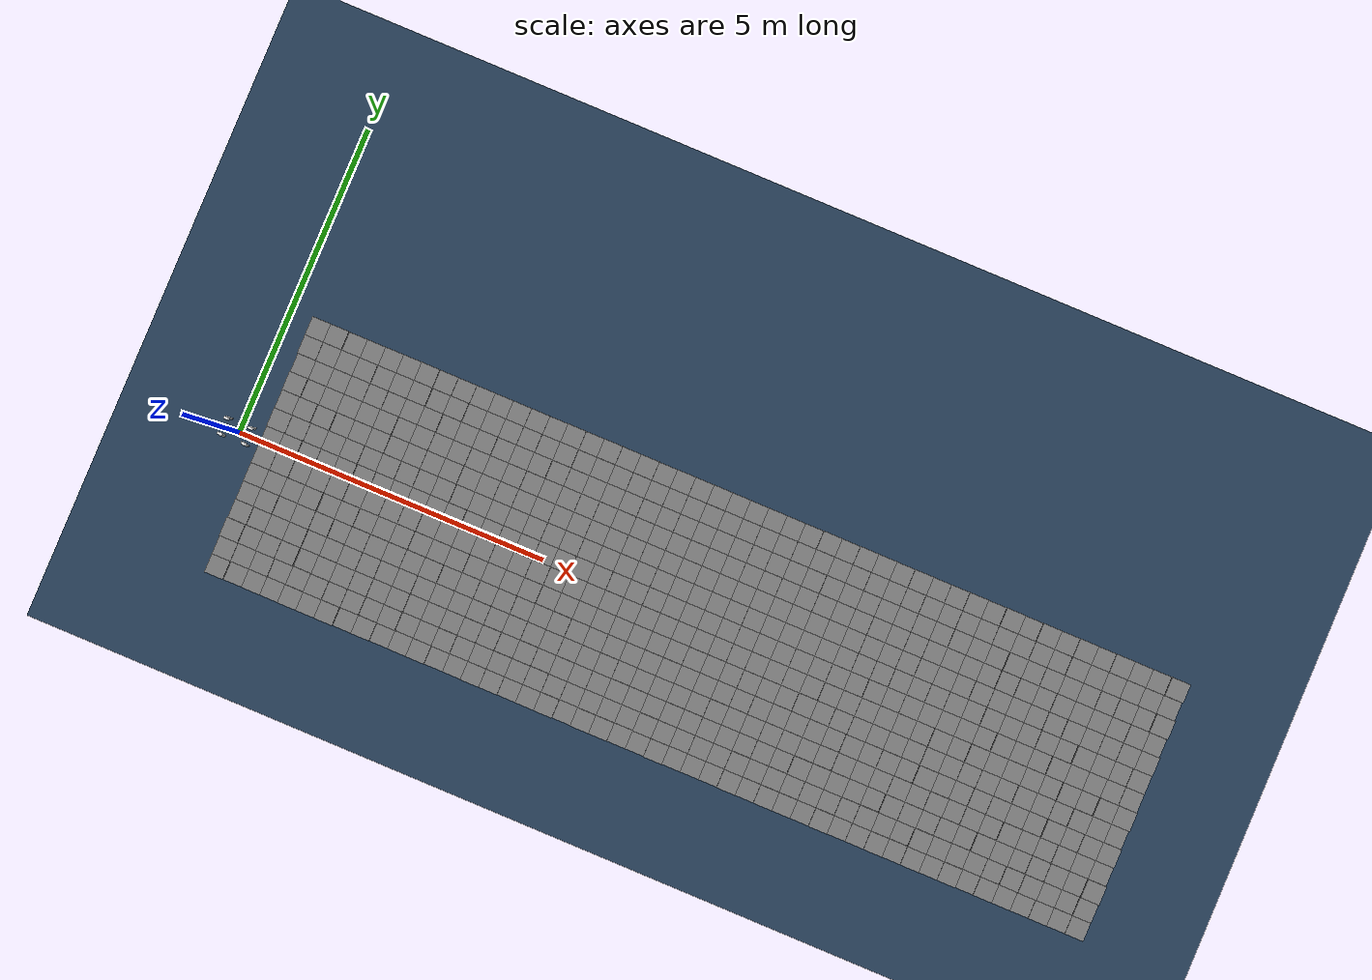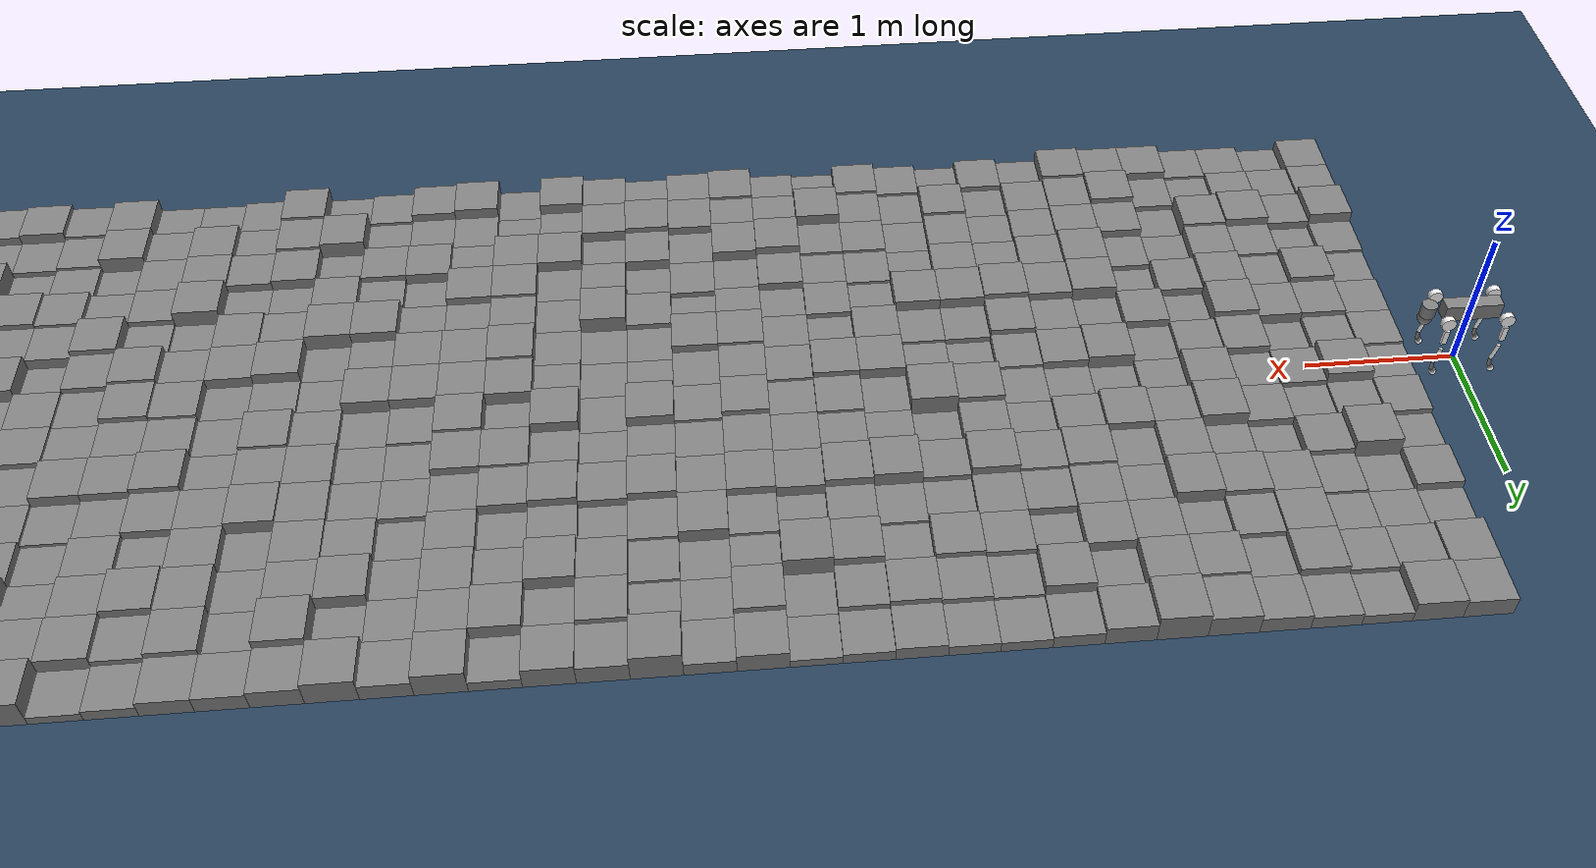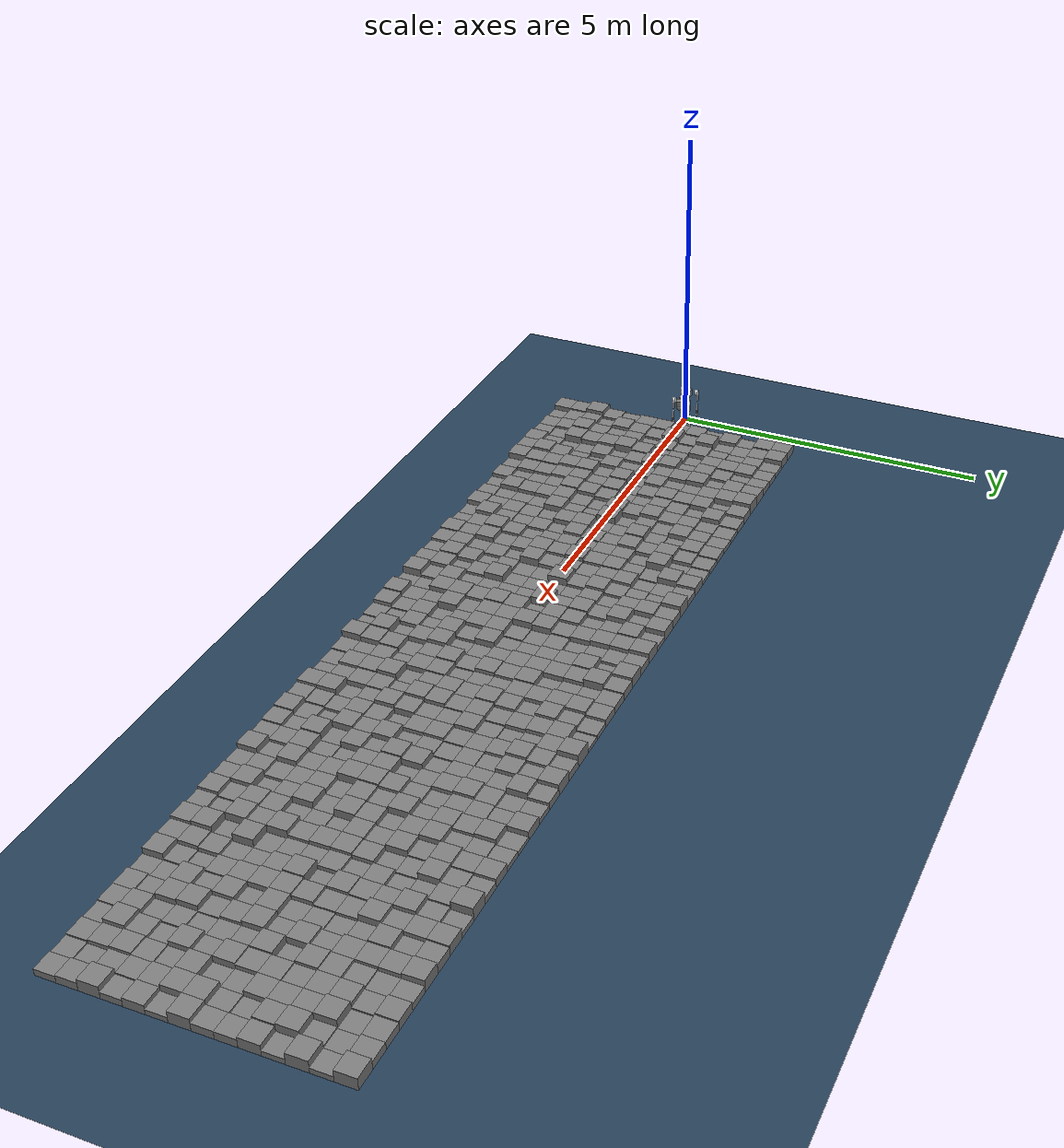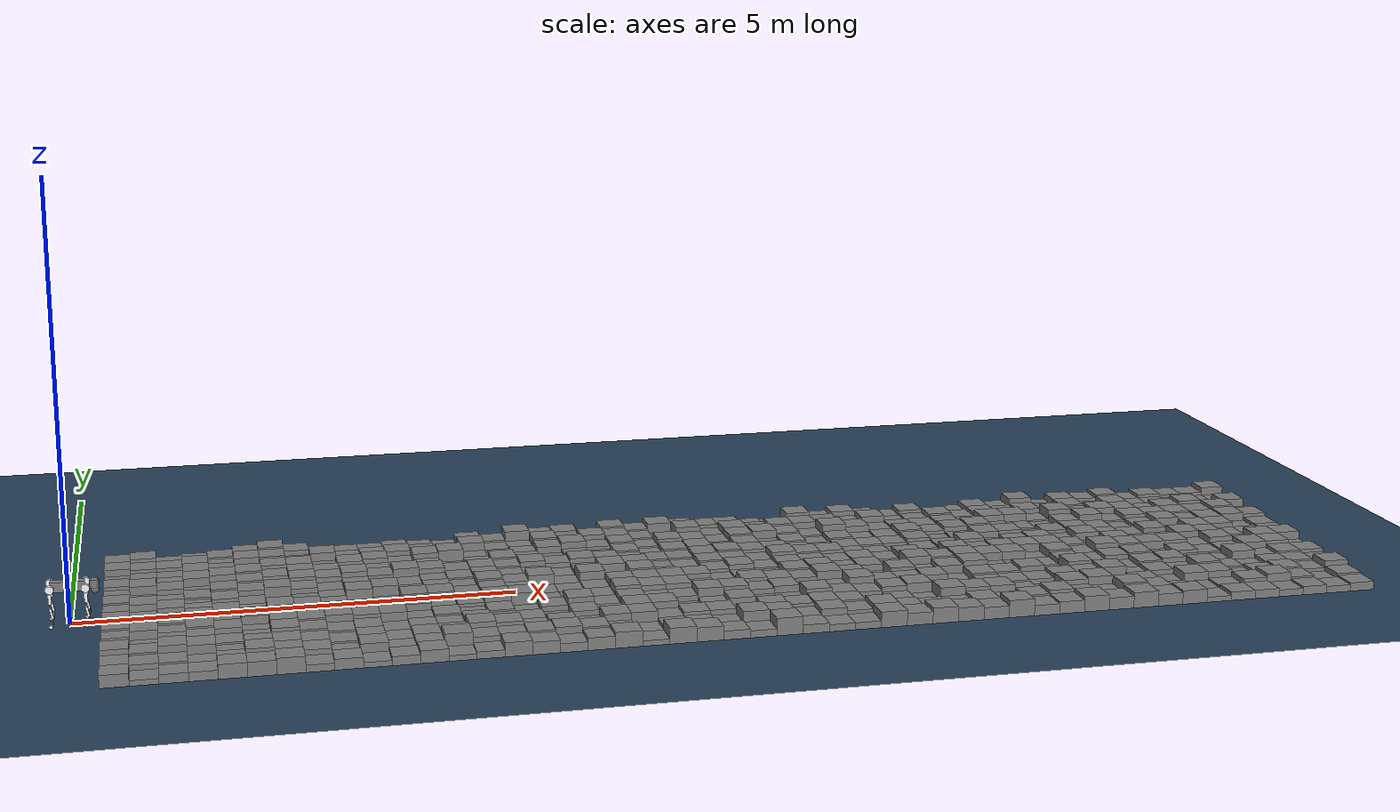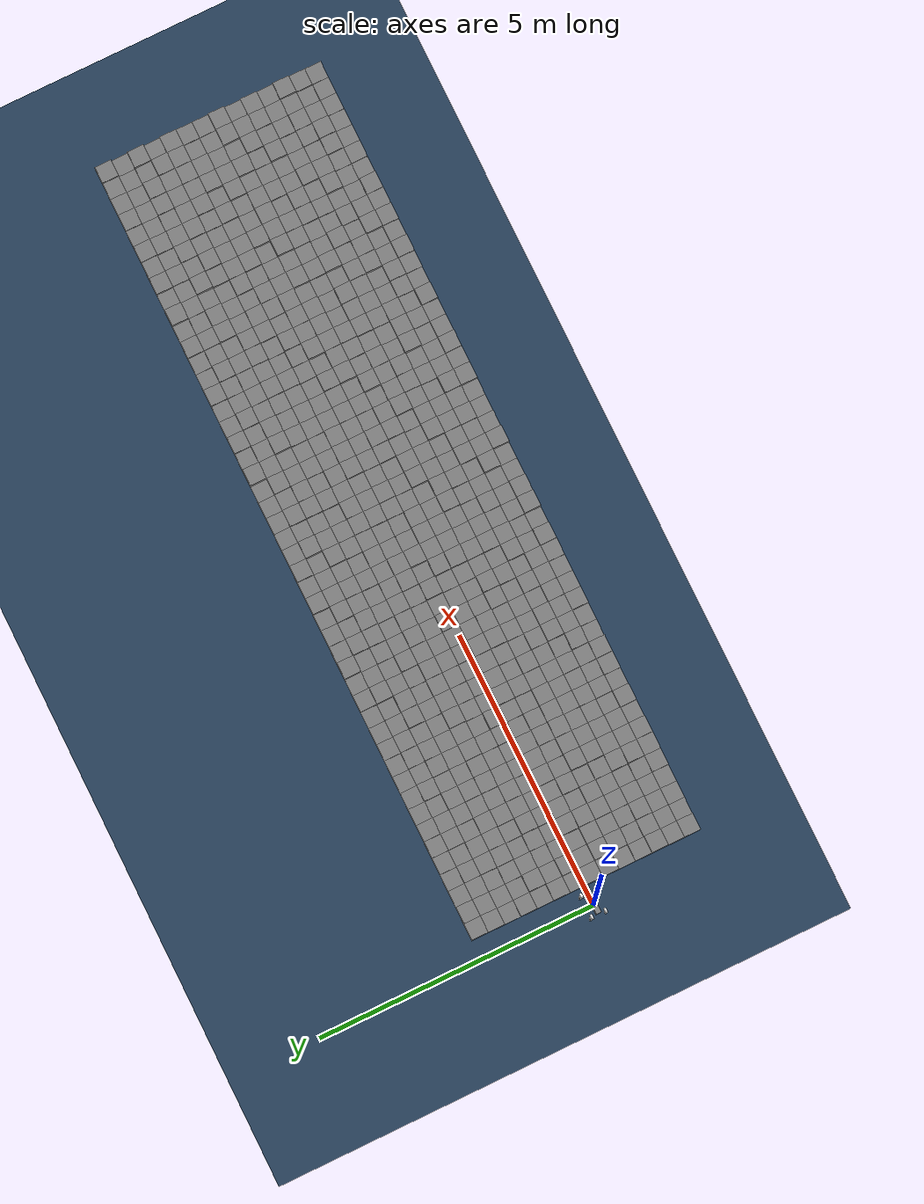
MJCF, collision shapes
<mujoco model="boxes">
  <include file="go2.xml" />

  <statistic center="0 0 0.1" extent="0.8" />

  <visual>
    <headlight diffuse="0.6 0.6 0.6" ambient="0.3 0.3 0.3" specular="0 0 0" />
    <rgba haze="0.15 0.25 0.35 1" />
    <global azimuth="-130" elevation="-20" />
  </visual>

  <asset>
    <texture type="skybox" builtin="gradient" rgb1="0.3 0.5 0.7" rgb2="0 0 0" width="512" height="3072" />
    <texture type="2d" name="groundplane" builtin="checker" mark="edge" rgb1="0.2 0.3 0.4" rgb2="0.1 0.2 0.3" markrgb="0.8 0.8 0.8" width="300" height="300" />
    <material name="groundplane" texture="groundplane" texuniform="true" texrepeat="5 5" reflectance="0.2" />
  </asset>

  <worldbody>
    <light pos="0 0 1.5" dir="0 0 -1" directional="true" />
    <geom name="floor" size="0 0 0.05" type="plane" material="groundplane" />

  <!-- Rough terrain: full coverage with dense bumps -->
  <geom pos="0.5 -2.0 0.07" type="box" size="0.15 0.15 0.07" />
  <geom pos="0.8 -2.0 0.03" type="box" size="0.15 0.15 0.03" />
  <geom pos="1.1 -2.0 0.05" type="box" size="0.15 0.15 0.05" />
  <geom pos="1.4 -2.0 0.05" type="box" size="0.15 0.15 0.05" />
  <geom pos="1.7 -2.0 0.08" type="box" size="0.15 0.15 0.08" />
  <geom pos="2.0 -2.0 0.08" type="box" size="0.15 0.15 0.08" />
  <geom pos="2.3 -2.0 0.09" type="box" size="0.15 0.15 0.09" />
  <geom pos="2.6 -2.0 0.04" type="box" size="0.15 0.15 0.04" />
  <geom pos="2.9 -2.0 0.06" type="box" size="0.15 0.15 0.06" />
  <geom pos="3.2 -2.0 0.03" type="box" size="0.15 0.15 0.03" />
  <geom pos="3.5 -2.0 0.05" type="box" size="0.15 0.15 0.05" />
  <geom pos="3.8 -2.0 0.07" type="box" size="0.15 0.15 0.07" />
  <geom pos="4.1 -2.0 0.03" type="box" size="0.15 0.15 0.03" />
  <geom pos="4.4 -2.0 0.04" type="box" size="0.15 0.15 0.04" />
  <geom pos="4.7 -2.0 0.08" type="box" size="0.15 0.15 0.08" />
  <geom pos="5.0 -2.0 0.07" type="box" size="0.15 0.15 0.07" />
  <geom pos="5.3 -2.0 0.05" type="box" size="0.15 0.15 0.05" />
  <geom pos="5.6 -2.0 0.07" type="box" size="0.15 0.15 0.07" />
  <geom pos="5.9 -2.0 0.09" type="box" size="0.15 0.15 0.09" />
  <geom pos="6.2 -2.0 0.03" type="box" size="0.15 0.15 0.03" />
  <geom pos="6.5 -2.0 0.09" type="box" size="0.15 0.15 0.09" />
  <geom pos="6.8 -2.0 0.08" type="box" size="0.15 0.15 0.08" />
  <geom pos="7.1 -2.0 0.05" type="box" size="0.15 0.15 0.05" />
  <geom pos="7.4 -2.0 0.04" type="box" size="0.15 0.15 0.04" />
  <geom pos="7.7 -2.0 0.1" type="box" size="0.15 0.15 0.1" />
  <geom pos="8.0 -2.0 0.05" type="box" size="0.15 0.15 0.05" />
  <geom pos="8.3 -2.0 0.04" type="box" size="0.15 0.15 0.04" />
  <geom pos="8.6 -2.0 0.04" type="box" size="0.15 0.15 0.04" />
  <geom pos="8.9 -2.0 0.09" type="box" size="0.15 0.15 0.09" />
  <geom pos="9.2 -2.0 0.07" type="box" size="0.15 0.15 0.07" />
  <geom pos="9.5 -2.0 0.09" type="box" size="0.15 0.15 0.09" />
  <geom pos="9.8 -2.0 0.08" type="box" size="0.15 0.15 0.08" />
  <geom pos="10.1 -2.0 0.07" type="box" size="0.15 0.15 0.07" />
  <geom pos="10.4 -2.0 0.1" type="box" size="0.15 0.15 0.1" />
  <geom pos="10.7 -2.0 0.06" type="box" size="0.15 0.15 0.06" />
  <geom pos="11.0 -2.0 0.07" type="box" size="0.15 0.15 0.07" />
  <geom pos="11.3 -2.0 0.09" type="box" size="0.15 0.15 0.09" />
  <geom pos="11.6 -2.0 0.07" type="box" size="0.15 0.15 0.07" />
  <geom pos="11.9 -2.0 0.09" type="box" size="0.15 0.15 0.09" />
  <geom pos="12.2 -2.0 0.07" type="box" size="0.15 0.15 0.07" />
  <geom pos="12.5 -2.0 0.08" type="box" size="0.15 0.15 0.08" />
  <geom pos="12.8 -2.0 0.03" type="box" size="0.15 0.15 0.03" />
  <geom pos="13.1 -2.0 0.05" type="box" size="0.15 0.15 0.05" />
  <geom pos="13.4 -2.0 0.05" type="box" size="0.15 0.15 0.05" />
  <geom pos="13.7 -2.0 0.04" type="box" size="0.15 0.15 0.04" />
  <geom pos="14.0 -2.0 0.05" type="box" size="0.15 0.15 0.05" />
  <geom pos="14.3 -2.0 0.04" type="box" size="0.15 0.15 0.04" />
  <geom pos="14.6 -2.0 0.05" type="box" size="0.15 0.15 0.05" />
  <geom pos="0.5 -1.7 0.07" type="box" size="0.15 0.15 0.07" />
  <geom pos="0.8 -1.7 0.06" type="box" size="0.15 0.15 0.06" />
  <geom pos="1.1 -1.7 0.06" type="box" size="0.15 0.15 0.06" />
  <geom pos="1.4 -1.7 0.04" type="box" size="0.15 0.15 0.04" />
  <geom pos="1.7 -1.7 0.05" type="box" size="0.15 0.15 0.05" />
  <geom pos="2.0 -1.7 0.1" type="box" size="0.15 0.15 0.1" />
  <geom pos="2.3 -1.7 0.08" type="box" size="0.15 0.15 0.08" />
  <geom pos="2.6 -1.7 0.07" type="box" size="0.15 0.15 0.07" />
  <geom pos="2.9 -1.7 0.04" type="box" size="0.15 0.15 0.04" />
  <geom pos="3.2 -1.7 0.08" type="box" size="0.15 0.15 0.08" />
  <geom pos="3.5 -1.7 0.04" type="box" size="0.15 0.15 0.04" />
  <geom pos="3.8 -1.7 0.06" type="box" size="0.15 0.15 0.06" />
  <geom pos="4.1 -1.7 0.1" type="box" size="0.15 0.15 0.1" />
  <geom pos="4.4 -1.7 0.07" type="box" size="0.15 0.15 0.07" />
  <geom pos="4.7 -1.7 0.07" type="box" size="0.15 0.15 0.07" />
  <geom pos="5.0 -1.7 0.08" type="box" size="0.15 0.15 0.08" />
  <geom pos="5.3 -1.7 0.09" type="box" size="0.15 0.15 0.09" />
  <geom pos="5.6 -1.7 0.08" type="box" size="0.15 0.15 0.08" />
  <geom pos="5.9 -1.7 0.05" type="box" size="0.15 0.15 0.05" />
  <geom pos="6.2 -1.7 0.03" type="box" size="0.15 0.15 0.03" />
  <geom pos="6.5 -1.7 0.05" type="box" size="0.15 0.15 0.05" />
  <geom pos="6.8 -1.7 0.05" type="box" size="0.15 0.15 0.05" />
  <geom pos="7.1 -1.7 0.04" type="box" size="0.15 0.15 0.04" />
  <geom pos="7.4 -1.7 0.1" type="box" size="0.15 0.15 0.1" />
  <geom pos="7.7 -1.7 0.09" type="box" size="0.15 0.15 0.09" />
  <geom pos="8.0 -1.7 0.05" type="box" size="0.15 0.15 0.05" />
  <geom pos="8.3 -1.7 0.08" type="box" size="0.15 0.15 0.08" />
  <geom pos="8.6 -1.7 0.06" type="box" size="0.15 0.15 0.06" />
  <geom pos="8.9 -1.7 0.09" type="box" size="0.15 0.15 0.09" />
  <geom pos="9.2 -1.7 0.06" type="box" size="0.15 0.15 0.06" />
  <geom pos="9.5 -1.7 0.05" type="box" size="0.15 0.15 0.05" />
  <geom pos="9.8 -1.7 0.05" type="box" size="0.15 0.15 0.05" />
  <geom pos="10.1 -1.7 0.07" type="box" size="0.15 0.15 0.07" />
  <geom pos="10.4 -1.7 0.05" type="box" size="0.15 0.15 0.05" />
  <geom pos="10.7 -1.7 0.07" type="box" size="0.15 0.15 0.07" />
  <geom pos="11.0 -1.7 0.09" type="box" size="0.15 0.15 0.09" />
  <geom pos="11.3 -1.7 0.06" type="box" size="0.15 0.15 0.06" />
  <geom pos="11.6 -1.7 0.05" type="box" size="0.15 0.15 0.05" />
  <geom pos="11.9 -1.7 0.1" type="box" size="0.15 0.15 0.1" />
  <geom pos="12.2 -1.7 0.07" type="box" size="0.15 0.15 0.07" />
  <geom pos="12.5 -1.7 0.04" type="box" size="0.15 0.15 0.04" />
  <geom pos="12.8 -1.7 0.03" type="box" size="0.15 0.15 0.03" />
  <geom pos="13.1 -1.7 0.04" type="box" size="0.15 0.15 0.04" />
  <geom pos="13.4 -1.7 0.07" type="box" size="0.15 0.15 0.07" />
  <geom pos="13.7 -1.7 0.09" type="box" size="0.15 0.15 0.09" />
  <geom pos="14.0 -1.7 0.06" type="box" size="0.15 0.15 0.06" />
  <geom pos="14.3 -1.7 0.03" type="box" size="0.15 0.15 0.03" />
  <geom pos="14.6 -1.7 0.06" type="box" size="0.15 0.15 0.06" />
  <geom pos="0.5 -1.4 0.1" type="box" size="0.15 0.15 0.1" />
  <geom pos="0.8 -1.4 0.07" type="box" size="0.15 0.15 0.07" />
  <geom pos="1.1 -1.4 0.1" type="box" size="0.15 0.15 0.1" />
  <geom pos="1.4 -1.4 0.09" type="box" size="0.15 0.15 0.09" />
  <geom pos="1.7 -1.4 0.03" type="box" size="0.15 0.15 0.03" />
  <geom pos="2.0 -1.4 0.08" type="box" size="0.15 0.15 0.08" />
  <geom pos="2.3 -1.4 0.08" type="box" size="0.15 0.15 0.08" />
  <geom pos="2.6 -1.4 0.07" type="box" size="0.15 0.15 0.07" />
  <geom pos="2.9 -1.4 0.05" type="box" size="0.15 0.15 0.05" />
  <geom pos="3.2 -1.4 0.07" type="box" size="0.15 0.15 0.07" />
  <geom pos="3.5 -1.4 0.04" type="box" size="0.15 0.15 0.04" />
  <geom pos="3.8 -1.4 0.06" type="box" size="0.15 0.15 0.06" />
  <geom pos="4.1 -1.4 0.06" type="box" size="0.15 0.15 0.06" />
  <geom pos="4.4 -1.4 0.1" type="box" size="0.15 0.15 0.1" />
  <geom pos="4.7 -1.4 0.09" type="box" size="0.15 0.15 0.09" />
  <geom pos="5.0 -1.4 0.05" type="box" size="0.15 0.15 0.05" />
  <geom pos="5.3 -1.4 0.07" type="box" size="0.15 0.15 0.07" />
  <geom pos="5.6 -1.4 0.04" type="box" size="0.15 0.15 0.04" />
  <geom pos="5.9 -1.4 0.09" type="box" size="0.15 0.15 0.09" />
  <geom pos="6.2 -1.4 0.09" type="box" size="0.15 0.15 0.09" />
  <geom pos="6.5 -1.4 0.05" type="box" size="0.15 0.15 0.05" />
  <geom pos="6.8 -1.4 0.07" type="box" size="0.15 0.15 0.07" />
  <geom pos="7.1 -1.4 0.07" type="box" size="0.15 0.15 0.07" />
  <geom pos="7.4 -1.4 0.04" type="box" size="0.15 0.15 0.04" />
  <geom pos="7.7 -1.4 0.08" type="box" size="0.15 0.15 0.08" />
  <geom pos="8.0 -1.4 0.07" type="box" size="0.15 0.15 0.07" />
  <geom pos="8.3 -1.4 0.08" type="box" size="0.15 0.15 0.08" />
  <geom pos="8.6 -1.4 0.07" type="box" size="0.15 0.15 0.07" />
  <geom pos="8.9 -1.4 0.03" type="box" size="0.15 0.15 0.03" />
  <geom pos="9.2 -1.4 0.05" type="box" size="0.15 0.15 0.05" />
  <geom pos="9.5 -1.4 0.03" type="box" size="0.15 0.15 0.03" />
  <geom pos="9.8 -1.4 0.1" type="box" size="0.15 0.15 0.1" />
  <geom pos="10.1 -1.4 0.09" type="box" size="0.15 0.15 0.09" />
  <geom pos="10.4 -1.4 0.09" type="box" size="0.15 0.15 0.09" />
  <geom pos="10.7 -1.4 0.05" type="box" size="0.15 0.15 0.05" />
  <geom pos="11.0 -1.4 0.03" type="box" size="0.15 0.15 0.03" />
  <geom pos="11.3 -1.4 0.09" type="box" size="0.15 0.15 0.09" />
  <geom pos="11.6 -1.4 0.1" type="box" size="0.15 0.15 0.1" />
  <geom pos="11.9 -1.4 0.04" type="box" size="0.15 0.15 0.04" />
  <geom pos="12.2 -1.4 0.06" type="box" size="0.15 0.15 0.06" />
  <geom pos="12.5 -1.4 0.03" type="box" size="0.15 0.15 0.03" />
  <geom pos="12.8 -1.4 0.08" type="box" size="0.15 0.15 0.08" />
  <geom pos="13.1 -1.4 0.08" type="box" size="0.15 0.15 0.08" />
  <geom pos="13.4 -1.4 0.04" type="box" size="0.15 0.15 0.04" />
  <geom pos="13.7 -1.4 0.06" type="box" size="0.15 0.15 0.06" />
  <geom pos="14.0 -1.4 0.07" type="box" size="0.15 0.15 0.07" />
  <geom pos="14.3 -1.4 0.05" type="box" size="0.15 0.15 0.05" />
  <geom pos="14.6 -1.4 0.09" type="box" size="0.15 0.15 0.09" />
  <geom pos="0.5 -1.1 0.06" type="box" size="0.15 0.15 0.06" />
  <geom pos="0.8 -1.1 0.04" type="box" size="0.15 0.15 0.04" />
  <geom pos="1.1 -1.1 0.07" type="box" size="0.15 0.15 0.07" />
  <geom pos="1.4 -1.1 0.08" type="box" size="0.15 0.15 0.08" />
  <geom pos="1.7 -1.1 0.04" type="box" size="0.15 0.15 0.04" />
  <geom pos="2.0 -1.1 0.05" type="box" size="0.15 0.15 0.05" />
  <geom pos="2.3 -1.1 0.1" type="box" size="0.15 0.15 0.1" />
  <geom pos="2.6 -1.1 0.08" type="box" size="0.15 0.15 0.08" />
  <geom pos="2.9 -1.1 0.06" type="box" size="0.15 0.15 0.06" />
  <geom pos="3.2 -1.1 0.07" type="box" size="0.15 0.15 0.07" />
  <geom pos="3.5 -1.1 0.04" type="box" size="0.15 0.15 0.04" />
  <geom pos="3.8 -1.1 0.05" type="box" size="0.15 0.15 0.05" />
  <geom pos="4.1 -1.1 0.05" type="box" size="0.15 0.15 0.05" />
  <geom pos="4.4 -1.1 0.07" type="box" size="0.15 0.15 0.07" />
  <geom pos="4.7 -1.1 0.05" type="box" size="0.15 0.15 0.05" />
  <geom pos="5.0 -1.1 0.05" type="box" size="0.15 0.15 0.05" />
  <geom pos="5.3 -1.1 0.03" type="box" size="0.15 0.15 0.03" />
  <geom pos="5.6 -1.1 0.07" type="box" size="0.15 0.15 0.07" />
  <geom pos="5.9 -1.1 0.05" type="box" size="0.15 0.15 0.05" />
  <geom pos="6.2 -1.1 0.09" type="box" size="0.15 0.15 0.09" />
  <geom pos="6.5 -1.1 0.09" type="box" size="0.15 0.15 0.09" />
  <geom pos="6.8 -1.1 0.03" type="box" size="0.15 0.15 0.03" />
  <geom pos="7.1 -1.1 0.05" type="box" size="0.15 0.15 0.05" />
  <geom pos="7.4 -1.1 0.08" type="box" size="0.15 0.15 0.08" />
  <geom pos="7.7 -1.1 0.04" type="box" size="0.15 0.15 0.04" />
  <geom pos="8.0 -1.1 0.04" type="box" size="0.15 0.15 0.04" />
  <geom pos="8.3 -1.1 0.1" type="box" size="0.15 0.15 0.1" />
  <geom pos="8.6 -1.1 0.07" type="box" size="0.15 0.15 0.07" />
  <geom pos="8.9 -1.1 0.06" type="box" size="0.15 0.15 0.06" />
  <geom pos="9.2 -1.1 0.08" type="box" size="0.15 0.15 0.08" />
  <geom pos="9.5 -1.1 0.09" type="box" size="0.15 0.15 0.09" />
  <geom pos="9.8 -1.1 0.04" type="box" size="0.15 0.15 0.04" />
  <geom pos="10.1 -1.1 0.04" type="box" size="0.15 0.15 0.04" />
  <geom pos="10.4 -1.1 0.06" type="box" size="0.15 0.15 0.06" />
  <geom pos="10.7 -1.1 0.06" type="box" size="0.15 0.15 0.06" />
  <geom pos="11.0 -1.1 0.06" type="box" size="0.15 0.15 0.06" />
  <geom pos="11.3 -1.1 0.08" type="box" size="0.15 0.15 0.08" />
  <geom pos="11.6 -1.1 0.08" type="box" size="0.15 0.15 0.08" />
  <geom pos="11.9 -1.1 0.1" type="box" size="0.15 0.15 0.1" />
  <geom pos="12.2 -1.1 0.04" type="box" size="0.15 0.15 0.04" />
  <geom pos="12.5 -1.1 0.06" type="box" size="0.15 0.15 0.06" />
  <geom pos="12.8 -1.1 0.05" type="box" size="0.15 0.15 0.05" />
  <geom pos="13.1 -1.1 0.09" type="box" size="0.15 0.15 0.09" />
  <geom pos="13.4 -1.1 0.05" type="box" size="0.15 0.15 0.05" />
  <geom pos="13.7 -1.1 0.04" type="box" size="0.15 0.15 0.04" />
  <geom pos="14.0 -1.1 0.06" type="box" size="0.15 0.15 0.06" />
  <geom pos="14.3 -1.1 0.06" type="box" size="0.15 0.15 0.06" />
  <geom pos="14.6 -1.1 0.05" type="box" size="0.15 0.15 0.05" />
  <geom pos="0.5 -0.8 0.05" type="box" size="0.15 0.15 0.05" />
  <geom pos="0.8 -0.8 0.09" type="box" size="0.15 0.15 0.09" />
  <geom pos="1.1 -0.8 0.06" type="box" size="0.15 0.15 0.06" />
  <geom pos="1.4 -0.8 0.09" type="box" size="0.15 0.15 0.09" />
  <geom pos="1.7 -0.8 0.07" type="box" size="0.15 0.15 0.07" />
  <geom pos="2.0 -0.8 0.03" type="box" size="0.15 0.15 0.03" />
  <geom pos="2.3 -0.8 0.1" type="box" size="0.15 0.15 0.1" />
  <geom pos="2.6 -0.8 0.09" type="box" size="0.15 0.15 0.09" />
  <geom pos="2.9 -0.8 0.1" type="box" size="0.15 0.15 0.1" />
  <geom pos="3.2 -0.8 0.09" type="box" size="0.15 0.15 0.09" />
  <geom pos="3.5 -0.8 0.09" type="box" size="0.15 0.15 0.09" />
  <geom pos="3.8 -0.8 0.04" type="box" size="0.15 0.15 0.04" />
  <geom pos="4.1 -0.8 0.06" type="box" size="0.15 0.15 0.06" />
  <geom pos="4.4 -0.8 0.04" type="box" size="0.15 0.15 0.04" />
  <geom pos="4.7 -0.8 0.06" type="box" size="0.15 0.15 0.06" />
  <geom pos="5.0 -0.8 0.03" type="box" size="0.15 0.15 0.03" />
  <geom pos="5.3 -0.8 0.06" type="box" size="0.15 0.15 0.06" />
  <geom pos="5.6 -0.8 0.1" type="box" size="0.15 0.15 0.1" />
  <geom pos="5.9 -0.8 0.05" type="box" size="0.15 0.15 0.05" />
  <geom pos="6.2 -0.8 0.08" type="box" size="0.15 0.15 0.08" />
  <geom pos="6.5 -0.8 0.06" type="box" size="0.15 0.15 0.06" />
  <geom pos="6.8 -0.8 0.06" type="box" size="0.15 0.15 0.06" />
  <geom pos="7.1 -0.8 0.1" type="box" size="0.15 0.15 0.1" />
  <geom pos="7.4 -0.8 0.1" type="box" size="0.15 0.15 0.1" />
  <geom pos="7.7 -0.8 0.07" type="box" size="0.15 0.15 0.07" />
  <geom pos="8.0 -0.8 0.08" type="box" size="0.15 0.15 0.08" />
  <geom pos="8.3 -0.8 0.04" type="box" size="0.15 0.15 0.04" />
  <geom pos="8.6 -0.8 0.05" type="box" size="0.15 0.15 0.05" />
  <geom pos="8.9 -0.8 0.1" type="box" size="0.15 0.15 0.1" />
  <geom pos="9.2 -0.8 0.07" type="box" size="0.15 0.15 0.07" />
  <geom pos="9.5 -0.8 0.07" type="box" size="0.15 0.15 0.07" />
  <geom pos="9.8 -0.8 0.08" type="box" size="0.15 0.15 0.08" />
  <geom pos="10.1 -0.8 0.03" type="box" size="0.15 0.15 0.03" />
  <geom pos="10.4 -0.8 0.07" type="box" size="0.15 0.15 0.07" />
  <geom pos="10.7 -0.8 0.07" type="box" size="0.15 0.15 0.07" />
  <geom pos="11.0 -0.8 0.09" type="box" size="0.15 0.15 0.09" />
  <geom pos="11.3 -0.8 0.04" type="box" size="0.15 0.15 0.04" />
  <geom pos="11.6 -0.8 0.1" type="box" size="0.15 0.15 0.1" />
  <geom pos="11.9 -0.8 0.04" type="box" size="0.15 0.15 0.04" />
  <geom pos="12.2 -0.8 0.04" type="box" size="0.15 0.15 0.04" />
  <geom pos="12.5 -0.8 0.07" type="box" size="0.15 0.15 0.07" />
  <geom pos="12.8 -0.8 0.08" type="box" size="0.15 0.15 0.08" />
  <geom pos="13.1 -0.8 0.05" type="box" size="0.15 0.15 0.05" />
  <geom pos="13.4 -0.8 0.04" type="box" size="0.15 0.15 0.04" />
  <geom pos="13.7 -0.8 0.09" type="box" size="0.15 0.15 0.09" />
  <geom pos="14.0 -0.8 0.05" type="box" size="0.15 0.15 0.05" />
  <geom pos="14.3 -0.8 0.07" type="box" size="0.15 0.15 0.07" />
  <geom pos="14.6 -0.8 0.07" type="box" size="0.15 0.15 0.07" />
  <geom pos="0.5 -0.5 0.06" type="box" size="0.15 0.15 0.06" />
  <geom pos="0.8 -0.5 0.07" type="box" size="0.15 0.15 0.07" />
  <geom pos="1.1 -0.5 0.07" type="box" size="0.15 0.15 0.07" />
  <geom pos="1.4 -0.5 0.1" type="box" size="0.15 0.15 0.1" />
  <geom pos="1.7 -0.5 0.04" type="box" size="0.15 0.15 0.04" />
  <geom pos="2.0 -0.5 0.08" type="box" size="0.15 0.15 0.08" />
  <geom pos="2.3 -0.5 0.05" type="box" size="0.15 0.15 0.05" />
  <geom pos="2.6 -0.5 0.06" type="box" size="0.15 0.15 0.06" />
  <geom pos="2.9 -0.5 0.08" type="box" size="0.15 0.15 0.08" />
  <geom pos="3.2 -0.5 0.05" type="box" size="0.15 0.15 0.05" />
  <geom pos="3.5 -0.5 0.05" type="box" size="0.15 0.15 0.05" />
  <geom pos="3.8 -0.5 0.08" type="box" size="0.15 0.15 0.08" />
  <geom pos="4.1 -0.5 0.04" type="box" size="0.15 0.15 0.04" />
  <geom pos="4.4 -0.5 0.06" type="box" size="0.15 0.15 0.06" />
  <geom pos="4.7 -0.5 0.1" type="box" size="0.15 0.15 0.1" />
  <geom pos="5.0 -0.5 0.1" type="box" size="0.15 0.15 0.1" />
  <geom pos="5.3 -0.5 0.04" type="box" size="0.15 0.15 0.04" />
  <geom pos="5.6 -0.5 0.04" type="box" size="0.15 0.15 0.04" />
  <geom pos="5.9 -0.5 0.05" type="box" size="0.15 0.15 0.05" />
  <geom pos="6.2 -0.5 0.1" type="box" size="0.15 0.15 0.1" />
  <geom pos="6.5 -0.5 0.09" type="box" size="0.15 0.15 0.09" />
  <geom pos="6.8 -0.5 0.09" type="box" size="0.15 0.15 0.09" />
  <geom pos="7.1 -0.5 0.06" type="box" size="0.15 0.15 0.06" />
  <geom pos="7.4 -0.5 0.04" type="box" size="0.15 0.15 0.04" />
  <geom pos="7.7 -0.5 0.09" type="box" size="0.15 0.15 0.09" />
  <geom pos="8.0 -0.5 0.08" type="box" size="0.15 0.15 0.08" />
  <geom pos="8.3 -0.5 0.07" type="box" size="0.15 0.15 0.07" />
  <geom pos="8.6 -0.5 0.1" type="box" size="0.15 0.15 0.1" />
  <geom pos="8.9 -0.5 0.08" type="box" size="0.15 0.15 0.08" />
  <geom pos="9.2 -0.5 0.03" type="box" size="0.15 0.15 0.03" />
  <geom pos="9.5 -0.5 0.09" type="box" size="0.15 0.15 0.09" />
  <geom pos="9.8 -0.5 0.05" type="box" size="0.15 0.15 0.05" />
  <geom pos="10.1 -0.5 0.08" type="box" size="0.15 0.15 0.08" />
  <geom pos="10.4 -0.5 0.1" type="box" size="0.15 0.15 0.1" />
  <geom pos="10.7 -0.5 0.04" type="box" size="0.15 0.15 0.04" />
  <geom pos="11.0 -0.5 0.04" type="box" size="0.15 0.15 0.04" />
  <geom pos="11.3 -0.5 0.04" type="box" size="0.15 0.15 0.04" />
  <geom pos="11.6 -0.5 0.07" type="box" size="0.15 0.15 0.07" />
  <geom pos="11.9 -0.5 0.05" type="box" size="0.15 0.15 0.05" />
  <geom pos="12.2 -0.5 0.07" type="box" size="0.15 0.15 0.07" />
  <geom pos="12.5 -0.5 0.08" type="box" size="0.15 0.15 0.08" />
  <geom pos="12.8 -0.5 0.04" type="box" size="0.15 0.15 0.04" />
  <geom pos="13.1 -0.5 0.07" type="box" size="0.15 0.15 0.07" />
  <geom pos="13.4 -0.5 0.05" type="box" size="0.15 0.15 0.05" />
  <geom pos="13.7 -0.5 0.06" type="box" size="0.15 0.15 0.06" />
  <geom pos="14.0 -0.5 0.09" type="box" size="0.15 0.15 0.09" />
  <geom pos="14.3 -0.5 0.09" type="box" size="0.15 0.15 0.09" />
  <geom pos="14.6 -0.5 0.04" type="box" size="0.15 0.15 0.04" />
  <geom pos="0.5 -0.2 0.06" type="box" size="0.15 0.15 0.06" />
  <geom pos="0.8 -0.2 0.05" type="box" size="0.15 0.15 0.05" />
  <geom pos="1.1 -0.2 0.03" type="box" size="0.15 0.15 0.03" />
  <geom pos="1.4 -0.2 0.08" type="box" size="0.15 0.15 0.08" />
  <geom pos="1.7 -0.2 0.07" type="box" size="0.15 0.15 0.07" />
  <geom pos="2.0 -0.2 0.05" type="box" size="0.15 0.15 0.05" />
  <geom pos="2.3 -0.2 0.08" type="box" size="0.15 0.15 0.08" />
  <geom pos="2.6 -0.2 0.07" type="box" size="0.15 0.15 0.07" />
  <geom pos="2.9 -0.2 0.06" type="box" size="0.15 0.15 0.06" />
  <geom pos="3.2 -0.2 0.03" type="box" size="0.15 0.15 0.03" />
  <geom pos="3.5 -0.2 0.04" type="box" size="0.15 0.15 0.04" />
  <geom pos="3.8 -0.2 0.09" type="box" size="0.15 0.15 0.09" />
  <geom pos="4.1 -0.2 0.09" type="box" size="0.15 0.15 0.09" />
  <geom pos="4.4 -0.2 0.07" type="box" size="0.15 0.15 0.07" />
  <geom pos="4.7 -0.2 0.09" type="box" size="0.15 0.15 0.09" />
  <geom pos="5.0 -0.2 0.07" type="box" size="0.15 0.15 0.07" />
  <geom pos="5.3 -0.2 0.04" type="box" size="0.15 0.15 0.04" />
  <geom pos="5.6 -0.2 0.04" type="box" size="0.15 0.15 0.04" />
  <geom pos="5.9 -0.2 0.05" type="box" size="0.15 0.15 0.05" />
  <geom pos="6.2 -0.2 0.09" type="box" size="0.15 0.15 0.09" />
  <geom pos="6.5 -0.2 0.09" type="box" size="0.15 0.15 0.09" />
  <geom pos="6.8 -0.2 0.09" type="box" size="0.15 0.15 0.09" />
  <geom pos="7.1 -0.2 0.09" type="box" size="0.15 0.15 0.09" />
  <geom pos="7.4 -0.2 0.04" type="box" size="0.15 0.15 0.04" />
  <geom pos="7.7 -0.2 0.05" type="box" size="0.15 0.15 0.05" />
  <geom pos="8.0 -0.2 0.04" type="box" size="0.15 0.15 0.04" />
  <geom pos="8.3 -0.2 0.08" type="box" size="0.15 0.15 0.08" />
  <geom pos="8.6 -0.2 0.09" type="box" size="0.15 0.15 0.09" />
  <geom pos="8.9 -0.2 0.06" type="box" size="0.15 0.15 0.06" />
  <geom pos="9.2 -0.2 0.07" type="box" size="0.15 0.15 0.07" />
  <geom pos="9.5 -0.2 0.04" type="box" size="0.15 0.15 0.04" />
  <geom pos="9.8 -0.2 0.1" type="box" size="0.15 0.15 0.1" />
  <geom pos="10.1 -0.2 0.09" type="box" size="0.15 0.15 0.09" />
  <geom pos="10.4 -0.2 0.1" type="box" size="0.15 0.15 0.1" />
  <geom pos="10.7 -0.2 0.09" type="box" size="0.15 0.15 0.09" />
  <geom pos="11.0 -0.2 0.09" type="box" size="0.15 0.15 0.09" />
  <geom pos="11.3 -0.2 0.03" type="box" size="0.15 0.15 0.03" />
  <geom pos="11.6 -0.2 0.08" type="box" size="0.15 0.15 0.08" />
  <geom pos="11.9 -0.2 0.05" type="box" size="0.15 0.15 0.05" />
  <geom pos="12.2 -0.2 0.1" type="box" size="0.15 0.15 0.1" />
  <geom pos="12.5 -0.2 0.09" type="box" size="0.15 0.15 0.09" />
  <geom pos="12.8 -0.2 0.09" type="box" size="0.15 0.15 0.09" />
  <geom pos="13.1 -0.2 0.09" type="box" size="0.15 0.15 0.09" />
  <geom pos="13.4 -0.2 0.05" type="box" size="0.15 0.15 0.05" />
  <geom pos="13.7 -0.2 0.09" type="box" size="0.15 0.15 0.09" />
  <geom pos="14.0 -0.2 0.04" type="box" size="0.15 0.15 0.04" />
  <geom pos="14.3 -0.2 0.09" type="box" size="0.15 0.15 0.09" />
  <geom pos="14.6 -0.2 0.09" type="box" size="0.15 0.15 0.09" />
  <geom pos="0.5 0.1 0.05" type="box" size="0.15 0.15 0.05" />
  <geom pos="0.8 0.1 0.09" type="box" size="0.15 0.15 0.09" />
  <geom pos="1.1 0.1 0.06" type="box" size="0.15 0.15 0.06" />
  <geom pos="1.4 0.1 0.05" type="box" size="0.15 0.15 0.05" />
  <geom pos="1.7 0.1 0.09" type="box" size="0.15 0.15 0.09" />
  <geom pos="2.0 0.1 0.05" type="box" size="0.15 0.15 0.05" />
  <geom pos="2.3 0.1 0.03" type="box" size="0.15 0.15 0.03" />
  <geom pos="2.6 0.1 0.04" type="box" size="0.15 0.15 0.04" />
  <geom pos="2.9 0.1 0.05" type="box" size="0.15 0.15 0.05" />
  <geom pos="3.2 0.1 0.09" type="box" size="0.15 0.15 0.09" />
  <geom pos="3.5 0.1 0.1" type="box" size="0.15 0.15 0.1" />
  <geom pos="3.8 0.1 0.05" type="box" size="0.15 0.15 0.05" />
  <geom pos="4.1 0.1 0.07" type="box" size="0.15 0.15 0.07" />
  <geom pos="4.4 0.1 0.06" type="box" size="0.15 0.15 0.06" />
  <geom pos="4.7 0.1 0.1" type="box" size="0.15 0.15 0.1" />
  <geom pos="5.0 0.1 0.07" type="box" size="0.15 0.15 0.07" />
  <geom pos="5.3 0.1 0.1" type="box" size="0.15 0.15 0.1" />
  <geom pos="5.6 0.1 0.04" type="box" size="0.15 0.15 0.04" />
  <geom pos="5.9 0.1 0.1" type="box" size="0.15 0.15 0.1" />
  <geom pos="6.2 0.1 0.04" type="box" size="0.15 0.15 0.04" />
  <geom pos="6.5 0.1 0.1" type="box" size="0.15 0.15 0.1" />
  <geom pos="6.8 0.1 0.05" type="box" size="0.15 0.15 0.05" />
  <geom pos="7.1 0.1 0.04" type="box" size="0.15 0.15 0.04" />
  <geom pos="7.4 0.1 0.06" type="box" size="0.15 0.15 0.06" />
  <geom pos="7.7 0.1 0.08" type="box" size="0.15 0.15 0.08" />
  <geom pos="8.0 0.1 0.05" type="box" size="0.15 0.15 0.05" />
  <geom pos="8.3 0.1 0.07" type="box" size="0.15 0.15 0.07" />
  <geom pos="8.6 0.1 0.07" type="box" size="0.15 0.15 0.07" />
  <geom pos="8.9 0.1 0.06" type="box" size="0.15 0.15 0.06" />
  <geom pos="9.2 0.1 0.07" type="box" size="0.15 0.15 0.07" />
  <geom pos="9.5 0.1 0.05" type="box" size="0.15 0.15 0.05" />
  <geom pos="9.8 0.1 0.08" type="box" size="0.15 0.15 0.08" />
  <geom pos="10.1 0.1 0.03" type="box" size="0.15 0.15 0.03" />
  <geom pos="10.4 0.1 0.09" type="box" size="0.15 0.15 0.09" />
  <geom pos="10.7 0.1 0.07" type="box" size="0.15 0.15 0.07" />
  <geom pos="11.0 0.1 0.08" type="box" size="0.15 0.15 0.08" />
  <geom pos="11.3 0.1 0.08" type="box" size="0.15 0.15 0.08" />
  <geom pos="11.6 0.1 0.08" type="box" size="0.15 0.15 0.08" />
  <geom pos="11.9 0.1 0.06" type="box" size="0.15 0.15 0.06" />
  <geom pos="12.2 0.1 0.03" type="box" size="0.15 0.15 0.03" />
  <geom pos="12.5 0.1 0.08" type="box" size="0.15 0.15 0.08" />
  <geom pos="12.8 0.1 0.05" type="box" size="0.15 0.15 0.05" />
  <geom pos="13.1 0.1 0.05" type="box" size="0.15 0.15 0.05" />
  <geom pos="13.4 0.1 0.09" type="box" size="0.15 0.15 0.09" />
  <geom pos="13.7 0.1 0.08" type="box" size="0.15 0.15 0.08" />
  <geom pos="14.0 0.1 0.05" type="box" size="0.15 0.15 0.05" />
  <geom pos="14.3 0.1 0.05" type="box" size="0.15 0.15 0.05" />
  <geom pos="14.6 0.1 0.06" type="box" size="0.15 0.15 0.06" />
  <geom pos="0.5 0.4 0.06" type="box" size="0.15 0.15 0.06" />
  <geom pos="0.8 0.4 0.05" type="box" size="0.15 0.15 0.05" />
  <geom pos="1.1 0.4 0.04" type="box" size="0.15 0.15 0.04" />
  <geom pos="1.4 0.4 0.06" type="box" size="0.15 0.15 0.06" />
  <geom pos="1.7 0.4 0.1" type="box" size="0.15 0.15 0.1" />
  <geom pos="2.0 0.4 0.08" type="box" size="0.15 0.15 0.08" />
  <geom pos="2.3 0.4 0.09" type="box" size="0.15 0.15 0.09" />
  <geom pos="2.6 0.4 0.07" type="box" size="0.15 0.15 0.07" />
  <geom pos="2.9 0.4 0.05" type="box" size="0.15 0.15 0.05" />
  <geom pos="3.2 0.4 0.07" type="box" size="0.15 0.15 0.07" />
  <geom pos="3.5 0.4 0.03" type="box" size="0.15 0.15 0.03" />
  <geom pos="3.8 0.4 0.05" type="box" size="0.15 0.15 0.05" />
  <geom pos="4.1 0.4 0.06" type="box" size="0.15 0.15 0.06" />
  <geom pos="4.4 0.4 0.07" type="box" size="0.15 0.15 0.07" />
  <geom pos="4.7 0.4 0.08" type="box" size="0.15 0.15 0.08" />
  <geom pos="5.0 0.4 0.06" type="box" size="0.15 0.15 0.06" />
  <geom pos="5.3 0.4 0.06" type="box" size="0.15 0.15 0.06" />
  <geom pos="5.6 0.4 0.04" type="box" size="0.15 0.15 0.04" />
  <geom pos="5.9 0.4 0.06" type="box" size="0.15 0.15 0.06" />
  <geom pos="6.2 0.4 0.09" type="box" size="0.15 0.15 0.09" />
  <geom pos="6.5 0.4 0.09" type="box" size="0.15 0.15 0.09" />
  <geom pos="6.8 0.4 0.04" type="box" size="0.15 0.15 0.04" />
  <geom pos="7.1 0.4 0.04" type="box" size="0.15 0.15 0.04" />
  <geom pos="7.4 0.4 0.07" type="box" size="0.15 0.15 0.07" />
  <geom pos="7.7 0.4 0.07" type="box" size="0.15 0.15 0.07" />
  <geom pos="8.0 0.4 0.05" type="box" size="0.15 0.15 0.05" />
  <geom pos="8.3 0.4 0.09" type="box" size="0.15 0.15 0.09" />
  <geom pos="8.6 0.4 0.08" type="box" size="0.15 0.15 0.08" />
  <geom pos="8.9 0.4 0.08" type="box" size="0.15 0.15 0.08" />
  <geom pos="9.2 0.4 0.05" type="box" size="0.15 0.15 0.05" />
  <geom pos="9.5 0.4 0.04" type="box" size="0.15 0.15 0.04" />
  <geom pos="9.8 0.4 0.03" type="box" size="0.15 0.15 0.03" />
  <geom pos="10.1 0.4 0.05" type="box" size="0.15 0.15 0.05" />
  <geom pos="10.4 0.4 0.06" type="box" size="0.15 0.15 0.06" />
  <geom pos="10.7 0.4 0.09" type="box" size="0.15 0.15 0.09" />
  <geom pos="11.0 0.4 0.04" type="box" size="0.15 0.15 0.04" />
  <geom pos="11.3 0.4 0.06" type="box" size="0.15 0.15 0.06" />
  <geom pos="11.6 0.4 0.07" type="box" size="0.15 0.15 0.07" />
  <geom pos="11.9 0.4 0.04" type="box" size="0.15 0.15 0.04" />
  <geom pos="12.2 0.4 0.08" type="box" size="0.15 0.15 0.08" />
  <geom pos="12.5 0.4 0.06" type="box" size="0.15 0.15 0.06" />
  <geom pos="12.8 0.4 0.05" type="box" size="0.15 0.15 0.05" />
  <geom pos="13.1 0.4 0.08" type="box" size="0.15 0.15 0.08" />
  <geom pos="13.4 0.4 0.03" type="box" size="0.15 0.15 0.03" />
  <geom pos="13.7 0.4 0.08" type="box" size="0.15 0.15 0.08" />
  <geom pos="14.0 0.4 0.08" type="box" size="0.15 0.15 0.08" />
  <geom pos="14.3 0.4 0.04" type="box" size="0.15 0.15 0.04" />
  <geom pos="14.6 0.4 0.06" type="box" size="0.15 0.15 0.06" />
  <geom pos="0.5 0.7 0.04" type="box" size="0.15 0.15 0.04" />
  <geom pos="0.8 0.7 0.1" type="box" size="0.15 0.15 0.1" />
  <geom pos="1.1 0.7 0.07" type="box" size="0.15 0.15 0.07" />
  <geom pos="1.4 0.7 0.03" type="box" size="0.15 0.15 0.03" />
  <geom pos="1.7 0.7 0.05" type="box" size="0.15 0.15 0.05" />
  <geom pos="2.0 0.7 0.09" type="box" size="0.15 0.15 0.09" />
  <geom pos="2.3 0.7 0.06" type="box" size="0.15 0.15 0.06" />
  <geom pos="2.6 0.7 0.09" type="box" size="0.15 0.15 0.09" />
  <geom pos="2.9 0.7 0.08" type="box" size="0.15 0.15 0.08" />
  <geom pos="3.2 0.7 0.1" type="box" size="0.15 0.15 0.1" />
  <geom pos="3.5 0.7 0.07" type="box" size="0.15 0.15 0.07" />
  <geom pos="3.8 0.7 0.1" type="box" size="0.15 0.15 0.1" />
  <geom pos="4.1 0.7 0.09" type="box" size="0.15 0.15 0.09" />
  <geom pos="4.4 0.7 0.07" type="box" size="0.15 0.15 0.07" />
  <geom pos="4.7 0.7 0.08" type="box" size="0.15 0.15 0.08" />
  <geom pos="5.0 0.7 0.07" type="box" size="0.15 0.15 0.07" />
  <geom pos="5.3 0.7 0.09" type="box" size="0.15 0.15 0.09" />
  <geom pos="5.6 0.7 0.07" type="box" size="0.15 0.15 0.07" />
  <geom pos="5.9 0.7 0.09" type="box" size="0.15 0.15 0.09" />
  <geom pos="6.2 0.7 0.08" type="box" size="0.15 0.15 0.08" />
  <geom pos="6.5 0.7 0.06" type="box" size="0.15 0.15 0.06" />
  <geom pos="6.8 0.7 0.05" type="box" size="0.15 0.15 0.05" />
  <geom pos="7.1 0.7 0.05" type="box" size="0.15 0.15 0.05" />
  <geom pos="7.4 0.7 0.07" type="box" size="0.15 0.15 0.07" />
  <geom pos="7.7 0.7 0.08" type="box" size="0.15 0.15 0.08" />
  <geom pos="8.0 0.7 0.07" type="box" size="0.15 0.15 0.07" />
  <geom pos="8.3 0.7 0.07" type="box" size="0.15 0.15 0.07" />
  <geom pos="8.6 0.7 0.05" type="box" size="0.15 0.15 0.05" />
  <geom pos="8.9 0.7 0.04" type="box" size="0.15 0.15 0.04" />
  <geom pos="9.2 0.7 0.05" type="box" size="0.15 0.15 0.05" />
  <geom pos="9.5 0.7 0.05" type="box" size="0.15 0.15 0.05" />
  <geom pos="9.8 0.7 0.05" type="box" size="0.15 0.15 0.05" />
  <geom pos="10.1 0.7 0.07" type="box" size="0.15 0.15 0.07" />
  <geom pos="10.4 0.7 0.04" type="box" size="0.15 0.15 0.04" />
  <geom pos="10.7 0.7 0.05" type="box" size="0.15 0.15 0.05" />
  <geom pos="11.0 0.7 0.08" type="box" size="0.15 0.15 0.08" />
  <geom pos="11.3 0.7 0.08" type="box" size="0.15 0.15 0.08" />
  <geom pos="11.6 0.7 0.03" type="box" size="0.15 0.15 0.03" />
  <geom pos="11.9 0.7 0.06" type="box" size="0.15 0.15 0.06" />
  <geom pos="12.2 0.7 0.07" type="box" size="0.15 0.15 0.07" />
  <geom pos="12.5 0.7 0.06" type="box" size="0.15 0.15 0.06" />
  <geom pos="12.8 0.7 0.04" type="box" size="0.15 0.15 0.04" />
  <geom pos="13.1 0.7 0.06" type="box" size="0.15 0.15 0.06" />
  <geom pos="13.4 0.7 0.09" type="box" size="0.15 0.15 0.09" />
  <geom pos="13.7 0.7 0.07" type="box" size="0.15 0.15 0.07" />
  <geom pos="14.0 0.7 0.08" type="box" size="0.15 0.15 0.08" />
  <geom pos="14.3 0.7 0.09" type="box" size="0.15 0.15 0.09" />
  <geom pos="14.6 0.7 0.08" type="box" size="0.15 0.15 0.08" />
  <geom pos="0.5 1.0 0.06" type="box" size="0.15 0.15 0.06" />
  <geom pos="0.8 1.0 0.03" type="box" size="0.15 0.15 0.03" />
  <geom pos="1.1 1.0 0.05" type="box" size="0.15 0.15 0.05" />
  <geom pos="1.4 1.0 0.08" type="box" size="0.15 0.15 0.08" />
  <geom pos="1.7 1.0 0.09" type="box" size="0.15 0.15 0.09" />
  <geom pos="2.0 1.0 0.1" type="box" size="0.15 0.15 0.1" />
  <geom pos="2.3 1.0 0.06" type="box" size="0.15 0.15 0.06" />
  <geom pos="2.6 1.0 0.08" type="box" size="0.15 0.15 0.08" />
  <geom pos="2.9 1.0 0.07" type="box" size="0.15 0.15 0.07" />
  <geom pos="3.2 1.0 0.07" type="box" size="0.15 0.15 0.07" />
  <geom pos="3.5 1.0 0.05" type="box" size="0.15 0.15 0.05" />
  <geom pos="3.8 1.0 0.05" type="box" size="0.15 0.15 0.05" />
  <geom pos="4.1 1.0 0.06" type="box" size="0.15 0.15 0.06" />
  <geom pos="4.4 1.0 0.03" type="box" size="0.15 0.15 0.03" />
  <geom pos="4.7 1.0 0.05" type="box" size="0.15 0.15 0.05" />
  <geom pos="5.0 1.0 0.08" type="box" size="0.15 0.15 0.08" />
  <geom pos="5.3 1.0 0.06" type="box" size="0.15 0.15 0.06" />
  <geom pos="5.6 1.0 0.04" type="box" size="0.15 0.15 0.04" />
  <geom pos="5.9 1.0 0.06" type="box" size="0.15 0.15 0.06" />
  <geom pos="6.2 1.0 0.04" type="box" size="0.15 0.15 0.04" />
  <geom pos="6.5 1.0 0.07" type="box" size="0.15 0.15 0.07" />
  <geom pos="6.8 1.0 0.03" type="box" size="0.15 0.15 0.03" />
  <geom pos="7.1 1.0 0.06" type="box" size="0.15 0.15 0.06" />
  <geom pos="7.4 1.0 0.07" type="box" size="0.15 0.15 0.07" />
  <geom pos="7.7 1.0 0.03" type="box" size="0.15 0.15 0.03" />
  <geom pos="8.0 1.0 0.07" type="box" size="0.15 0.15 0.07" />
  <geom pos="8.3 1.0 0.04" type="box" size="0.15 0.15 0.04" />
  <geom pos="8.6 1.0 0.06" type="box" size="0.15 0.15 0.06" />
  <geom pos="8.9 1.0 0.03" type="box" size="0.15 0.15 0.03" />
  <geom pos="9.2 1.0 0.06" type="box" size="0.15 0.15 0.06" />
  <geom pos="9.5 1.0 0.04" type="box" size="0.15 0.15 0.04" />
  <geom pos="9.8 1.0 0.05" type="box" size="0.15 0.15 0.05" />
  <geom pos="10.1 1.0 0.08" type="box" size="0.15 0.15 0.08" />
  <geom pos="10.4 1.0 0.06" type="box" size="0.15 0.15 0.06" />
  <geom pos="10.7 1.0 0.08" type="box" size="0.15 0.15 0.08" />
  <geom pos="11.0 1.0 0.09" type="box" size="0.15 0.15 0.09" />
  <geom pos="11.3 1.0 0.05" type="box" size="0.15 0.15 0.05" />
  <geom pos="11.6 1.0 0.04" type="box" size="0.15 0.15 0.04" />
  <geom pos="11.9 1.0 0.03" type="box" size="0.15 0.15 0.03" />
  <geom pos="12.2 1.0 0.07" type="box" size="0.15 0.15 0.07" />
  <geom pos="12.5 1.0 0.1" type="box" size="0.15 0.15 0.1" />
  <geom pos="12.8 1.0 0.05" type="box" size="0.15 0.15 0.05" />
  <geom pos="13.1 1.0 0.08" type="box" size="0.15 0.15 0.08" />
  <geom pos="13.4 1.0 0.08" type="box" size="0.15 0.15 0.08" />
  <geom pos="13.7 1.0 0.08" type="box" size="0.15 0.15 0.08" />
  <geom pos="14.0 1.0 0.08" type="box" size="0.15 0.15 0.08" />
  <geom pos="14.3 1.0 0.1" type="box" size="0.15 0.15 0.1" />
  <geom pos="14.6 1.0 0.04" type="box" size="0.15 0.15 0.04" />
  <geom pos="0.5 1.3 0.03" type="box" size="0.15 0.15 0.03" />
  <geom pos="0.8 1.3 0.04" type="box" size="0.15 0.15 0.04" />
  <geom pos="1.1 1.3 0.04" type="box" size="0.15 0.15 0.04" />
  <geom pos="1.4 1.3 0.08" type="box" size="0.15 0.15 0.08" />
  <geom pos="1.7 1.3 0.07" type="box" size="0.15 0.15 0.07" />
  <geom pos="2.0 1.3 0.05" type="box" size="0.15 0.15 0.05" />
  <geom pos="2.3 1.3 0.08" type="box" size="0.15 0.15 0.08" />
  <geom pos="2.6 1.3 0.08" type="box" size="0.15 0.15 0.08" />
  <geom pos="2.9 1.3 0.04" type="box" size="0.15 0.15 0.04" />
  <geom pos="3.2 1.3 0.07" type="box" size="0.15 0.15 0.07" />
  <geom pos="3.5 1.3 0.08" type="box" size="0.15 0.15 0.08" />
  <geom pos="3.8 1.3 0.04" type="box" size="0.15 0.15 0.04" />
  <geom pos="4.1 1.3 0.09" type="box" size="0.15 0.15 0.09" />
  <geom pos="4.4 1.3 0.1" type="box" size="0.15 0.15 0.1" />
  <geom pos="4.7 1.3 0.04" type="box" size="0.15 0.15 0.04" />
  <geom pos="5.0 1.3 0.03" type="box" size="0.15 0.15 0.03" />
  <geom pos="5.3 1.3 0.05" type="box" size="0.15 0.15 0.05" />
  <geom pos="5.6 1.3 0.08" type="box" size="0.15 0.15 0.08" />
  <geom pos="5.9 1.3 0.1" type="box" size="0.15 0.15 0.1" />
  <geom pos="6.2 1.3 0.06" type="box" size="0.15 0.15 0.06" />
  <geom pos="6.5 1.3 0.08" type="box" size="0.15 0.15 0.08" />
  <geom pos="6.8 1.3 0.04" type="box" size="0.15 0.15 0.04" />
  <geom pos="7.1 1.3 0.08" type="box" size="0.15 0.15 0.08" />
  <geom pos="7.4 1.3 0.07" type="box" size="0.15 0.15 0.07" />
  <geom pos="7.7 1.3 0.04" type="box" size="0.15 0.15 0.04" />
  <geom pos="8.0 1.3 0.08" type="box" size="0.15 0.15 0.08" />
  <geom pos="8.3 1.3 0.09" type="box" size="0.15 0.15 0.09" />
  <geom pos="8.6 1.3 0.07" type="box" size="0.15 0.15 0.07" />
  <geom pos="8.9 1.3 0.04" type="box" size="0.15 0.15 0.04" />
  <geom pos="9.2 1.3 0.1" type="box" size="0.15 0.15 0.1" />
  <geom pos="9.5 1.3 0.08" type="box" size="0.15 0.15 0.08" />
  <geom pos="9.8 1.3 0.05" type="box" size="0.15 0.15 0.05" />
  <geom pos="10.1 1.3 0.06" type="box" size="0.15 0.15 0.06" />
  <geom pos="10.4 1.3 0.06" type="box" size="0.15 0.15 0.06" />
  <geom pos="10.7 1.3 0.07" type="box" size="0.15 0.15 0.07" />
  <geom pos="11.0 1.3 0.05" type="box" size="0.15 0.15 0.05" />
  <geom pos="11.3 1.3 0.09" type="box" size="0.15 0.15 0.09" />
  <geom pos="11.6 1.3 0.09" type="box" size="0.15 0.15 0.09" />
  <geom pos="11.9 1.3 0.04" type="box" size="0.15 0.15 0.04" />
  <geom pos="12.2 1.3 0.1" type="box" size="0.15 0.15 0.1" />
  <geom pos="12.5 1.3 0.07" type="box" size="0.15 0.15 0.07" />
  <geom pos="12.8 1.3 0.09" type="box" size="0.15 0.15 0.09" />
  <geom pos="13.1 1.3 0.08" type="box" size="0.15 0.15 0.08" />
  <geom pos="13.4 1.3 0.06" type="box" size="0.15 0.15 0.06" />
  <geom pos="13.7 1.3 0.08" type="box" size="0.15 0.15 0.08" />
  <geom pos="14.0 1.3 0.1" type="box" size="0.15 0.15 0.1" />
  <geom pos="14.3 1.3 0.05" type="box" size="0.15 0.15 0.05" />
  <geom pos="14.6 1.3 0.09" type="box" size="0.15 0.15 0.09" />
  <geom pos="0.5 1.6 0.07" type="box" size="0.15 0.15 0.07" />
  <geom pos="0.8 1.6 0.06" type="box" size="0.15 0.15 0.06" />
  <geom pos="1.1 1.6 0.06" type="box" size="0.15 0.15 0.06" />
  <geom pos="1.4 1.6 0.08" type="box" size="0.15 0.15 0.08" />
  <geom pos="1.7 1.6 0.05" type="box" size="0.15 0.15 0.05" />
  <geom pos="2.0 1.6 0.09" type="box" size="0.15 0.15 0.09" />
  <geom pos="2.3 1.6 0.09" type="box" size="0.15 0.15 0.09" />
  <geom pos="2.6 1.6 0.04" type="box" size="0.15 0.15 0.04" />
  <geom pos="2.9 1.6 0.09" type="box" size="0.15 0.15 0.09" />
  <geom pos="3.2 1.6 0.05" type="box" size="0.15 0.15 0.05" />
  <geom pos="3.5 1.6 0.06" type="box" size="0.15 0.15 0.06" />
  <geom pos="3.8 1.6 0.07" type="box" size="0.15 0.15 0.07" />
  <geom pos="4.1 1.6 0.06" type="box" size="0.15 0.15 0.06" />
  <geom pos="4.4 1.6 0.03" type="box" size="0.15 0.15 0.03" />
  <geom pos="4.7 1.6 0.09" type="box" size="0.15 0.15 0.09" />
  <geom pos="5.0 1.6 0.04" type="box" size="0.15 0.15 0.04" />
  <geom pos="5.3 1.6 0.04" type="box" size="0.15 0.15 0.04" />
  <geom pos="5.6 1.6 0.09" type="box" size="0.15 0.15 0.09" />
  <geom pos="5.9 1.6 0.05" type="box" size="0.15 0.15 0.05" />
  <geom pos="6.2 1.6 0.09" type="box" size="0.15 0.15 0.09" />
  <geom pos="6.5 1.6 0.08" type="box" size="0.15 0.15 0.08" />
  <geom pos="6.8 1.6 0.05" type="box" size="0.15 0.15 0.05" />
  <geom pos="7.1 1.6 0.03" type="box" size="0.15 0.15 0.03" />
  <geom pos="7.4 1.6 0.1" type="box" size="0.15 0.15 0.1" />
  <geom pos="7.7 1.6 0.04" type="box" size="0.15 0.15 0.04" />
  <geom pos="8.0 1.6 0.08" type="box" size="0.15 0.15 0.08" />
  <geom pos="8.3 1.6 0.06" type="box" size="0.15 0.15 0.06" />
  <geom pos="8.6 1.6 0.08" type="box" size="0.15 0.15 0.08" />
  <geom pos="8.9 1.6 0.08" type="box" size="0.15 0.15 0.08" />
  <geom pos="9.2 1.6 0.08" type="box" size="0.15 0.15 0.08" />
  <geom pos="9.5 1.6 0.06" type="box" size="0.15 0.15 0.06" />
  <geom pos="9.8 1.6 0.09" type="box" size="0.15 0.15 0.09" />
  <geom pos="10.1 1.6 0.04" type="box" size="0.15 0.15 0.04" />
  <geom pos="10.4 1.6 0.05" type="box" size="0.15 0.15 0.05" />
  <geom pos="10.7 1.6 0.08" type="box" size="0.15 0.15 0.08" />
  <geom pos="11.0 1.6 0.05" type="box" size="0.15 0.15 0.05" />
  <geom pos="11.3 1.6 0.07" type="box" size="0.15 0.15 0.07" />
  <geom pos="11.6 1.6 0.06" type="box" size="0.15 0.15 0.06" />
  <geom pos="11.9 1.6 0.07" type="box" size="0.15 0.15 0.07" />
  <geom pos="12.2 1.6 0.06" type="box" size="0.15 0.15 0.06" />
  <geom pos="12.5 1.6 0.08" type="box" size="0.15 0.15 0.08" />
  <geom pos="12.8 1.6 0.05" type="box" size="0.15 0.15 0.05" />
  <geom pos="13.1 1.6 0.08" type="box" size="0.15 0.15 0.08" />
  <geom pos="13.4 1.6 0.05" type="box" size="0.15 0.15 0.05" />
  <geom pos="13.7 1.6 0.05" type="box" size="0.15 0.15 0.05" />
  <geom pos="14.0 1.6 0.04" type="box" size="0.15 0.15 0.04" />
  <geom pos="14.3 1.6 0.04" type="box" size="0.15 0.15 0.04" />
  <geom pos="14.6 1.6 0.04" type="box" size="0.15 0.15 0.04" />
  <geom pos="0.5 1.9 0.07" type="box" size="0.15 0.15 0.07" />
  <geom pos="0.8 1.9 0.08" type="box" size="0.15 0.15 0.08" />
  <geom pos="1.1 1.9 0.04" type="box" size="0.15 0.15 0.04" />
  <geom pos="1.4 1.9 0.05" type="box" size="0.15 0.15 0.05" />
  <geom pos="1.7 1.9 0.06" type="box" size="0.15 0.15 0.06" />
  <geom pos="2.0 1.9 0.08" type="box" size="0.15 0.15 0.08" />
  <geom pos="2.3 1.9 0.1" type="box" size="0.15 0.15 0.1" />
  <geom pos="2.6 1.9 0.07" type="box" size="0.15 0.15 0.07" />
  <geom pos="2.9 1.9 0.05" type="box" size="0.15 0.15 0.05" />
  <geom pos="3.2 1.9 0.04" type="box" size="0.15 0.15 0.04" />
  <geom pos="3.5 1.9 0.04" type="box" size="0.15 0.15 0.04" />
  <geom pos="3.8 1.9 0.05" type="box" size="0.15 0.15 0.05" />
  <geom pos="4.1 1.9 0.04" type="box" size="0.15 0.15 0.04" />
  <geom pos="4.4 1.9 0.03" type="box" size="0.15 0.15 0.03" />
  <geom pos="4.7 1.9 0.07" type="box" size="0.15 0.15 0.07" />
  <geom pos="5.0 1.9 0.05" type="box" size="0.15 0.15 0.05" />
  <geom pos="5.3 1.9 0.1" type="box" size="0.15 0.15 0.1" />
  <geom pos="5.6 1.9 0.07" type="box" size="0.15 0.15 0.07" />
  <geom pos="5.9 1.9 0.08" type="box" size="0.15 0.15 0.08" />
  <geom pos="6.2 1.9 0.04" type="box" size="0.15 0.15 0.04" />
  <geom pos="6.5 1.9 0.09" type="box" size="0.15 0.15 0.09" />
  <geom pos="6.8 1.9 0.06" type="box" size="0.15 0.15 0.06" />
  <geom pos="7.1 1.9 0.09" type="box" size="0.15 0.15 0.09" />
  <geom pos="7.4 1.9 0.07" type="box" size="0.15 0.15 0.07" />
  <geom pos="7.7 1.9 0.06" type="box" size="0.15 0.15 0.06" />
  <geom pos="8.0 1.9 0.06" type="box" size="0.15 0.15 0.06" />
  <geom pos="8.3 1.9 0.04" type="box" size="0.15 0.15 0.04" />
  <geom pos="8.6 1.9 0.03" type="box" size="0.15 0.15 0.03" />
  <geom pos="8.9 1.9 0.1" type="box" size="0.15 0.15 0.1" />
  <geom pos="9.2 1.9 0.06" type="box" size="0.15 0.15 0.06" />
  <geom pos="9.5 1.9 0.09" type="box" size="0.15 0.15 0.09" />
  <geom pos="9.8 1.9 0.06" type="box" size="0.15 0.15 0.06" />
  <geom pos="10.1 1.9 0.04" type="box" size="0.15 0.15 0.04" />
  <geom pos="10.4 1.9 0.07" type="box" size="0.15 0.15 0.07" />
  <geom pos="10.7 1.9 0.03" type="box" size="0.15 0.15 0.03" />
  <geom pos="11.0 1.9 0.04" type="box" size="0.15 0.15 0.04" />
  <geom pos="11.3 1.9 0.07" type="box" size="0.15 0.15 0.07" />
  <geom pos="11.6 1.9 0.05" type="box" size="0.15 0.15 0.05" />
  <geom pos="11.9 1.9 0.1" type="box" size="0.15 0.15 0.1" />
  <geom pos="12.2 1.9 0.04" type="box" size="0.15 0.15 0.04" />
  <geom pos="12.5 1.9 0.08" type="box" size="0.15 0.15 0.08" />
  <geom pos="12.8 1.9 0.07" type="box" size="0.15 0.15 0.07" />
  <geom pos="13.1 1.9 0.09" type="box" size="0.15 0.15 0.09" />
  <geom pos="13.4 1.9 0.05" type="box" size="0.15 0.15 0.05" />
  <geom pos="13.7 1.9 0.07" type="box" size="0.15 0.15 0.07" />
  <geom pos="14.0 1.9 0.06" type="box" size="0.15 0.15 0.06" />
  <geom pos="14.3 1.9 0.06" type="box" size="0.15 0.15 0.06" />
  <geom pos="14.6 1.9 0.09" type="box" size="0.15 0.15 0.09" />
  </worldbody>
</mujoco>

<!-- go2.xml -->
<mujoco model="go2_description">

  <compiler angle="radian" meshdir="assets"/>

  <statistic meansize="0.144785" extent="1.23314" center="0.025392 2.0634e-05 -0.245975"/>
  <default>
    <joint damping="0.001" armature="0.01" frictionloss="0.1"/>
    <default class="visual">
        <geom type="mesh" contype="0" conaffinity="0" group="2"/>
    </default>
  </default>

  <asset>
    <material name="metal" rgba=".9 .95 .95 1" />
    <material name="black" rgba="0 0 0 1" />
    <material name="white" rgba="1 1 1 1" />
    <material name="gray" rgba="0.671705 0.692426 0.774270 1" />

    <mesh file="base_0.obj" />
    <mesh file="base_1.obj" />
    <mesh file="base_2.obj" />
    <mesh file="base_3.obj" />
    <mesh file="base_4.obj" />
    <mesh file="hip_0.obj" />
    <mesh file="hip_1.obj" />
    <mesh file="thigh_0.obj" />
    <mesh file="thigh_1.obj" />
    <mesh file="thigh_mirror_0.obj" />
    <mesh file="thigh_mirror_1.obj" />
    <mesh file="calf_0.obj" />
    <mesh file="calf_1.obj" />
    <mesh file="calf_mirror_0.obj" />
    <mesh file="calf_mirror_1.obj" />
    <mesh file="foot.obj" />
  </asset>

  <worldbody>

    <body name="base" pos="0 0 0.445">
      <inertial pos="0.021112 0 -0.005366"
                mass="6.921"
                diaginertia="0.02448 0.098077 0.107" />
      <freejoint name="root"/>
      <geom mesh="base_0" material="black" class="visual" />
      <geom mesh="base_1" material="black" class="visual" />
      <geom mesh="base_2" material="black" class="visual" />
      <geom mesh="base_3" material="white" class="visual" />
      <geom mesh="base_4" material="gray" class="visual" />

      <geom name="base_box"      type="box"      size="0.1881 0.04675 0.057"/>
      <geom name="base_cyl1"     type="cylinder" size="0.05 0.045"   pos="0.285 0 0.01"/>
      <geom name="base_sphere1"  type="sphere"   size="0.047"        pos="0.293 0 -0.06"/>

      <body name="FL_hip" pos="0.1934 0.0465 0">
        <inertial pos="-0.0054 0.00194 -0.000105" quat="0.497014 0.499245 0.505462 0.498237" mass="0.678" diaginertia="0.00088403 0.000596003 0.000479967"/>
        <joint name="FL_hip_joint" pos="0 0 0" axis="1 0 0" range="-1.0472 1.0472" actuatorfrcrange="-23.7 23.7"/>
        <geom mesh="hip_0" material="metal" class="visual" />
        <geom mesh="hip_1" material="gray" class="visual" />
        <geom size="0.046 0.02" pos="0 0.08 0" quat="0.707107 0.707107 0 0" type="cylinder" rgba="1 1 1 1"/>

        <body name="FL_thigh" pos="0 0.0955 0">
        <inertial pos="-0.00374 -0.0223 -0.0327" quat="0.829533 0.0847635 -0.0200632 0.551623" mass="1.152" diaginertia="0.00594973 0.00584149 0.000878787"/>
        <joint name="FL_thigh_joint" pos="0 0 0" axis="0 1 0" range="-1.5708 3.4907" actuatorfrcrange="-23.7 23.7"/>
        <geom mesh="thigh_0" material="metal" class="visual" />
        <geom mesh="thigh_1" material="gray" class="visual" />
        <geom size="0.055 0.01225 0.017" pos="0 0 -0.1065" quat="0.707107 0 0.707107 0" type="box" rgba="1 1 1 1"/>
        <body name="FL_calf" pos="0 0 -0.213">
        <inertial pos="0.00629595 -0.000622121 -0.141417" quat="0.710672 0.00154099 -0.00450087 0.703508" mass="0.241352" diaginertia="0.0014901 0.00146356 5.31397e-05"/>
        <joint name="FL_calf_joint" pos="0 0 0" axis="0 1 0" range="-2.7227 -0.83776" actuatorfrcrange="-35.55 35.55"/>
        <geom mesh="calf_0" material="gray" class="visual" />
        <geom mesh="calf_1" material="black" class="visual" />
        <geom size="0.012 0.06" pos="0.008 0 -0.06" quat="0.994493 0 -0.104807 0" type="cylinder" rgba="1 1 1 1"/>
        <geom size="0.011 0.0325" pos="0.02 0 -0.148" quat="0.999688 0 0.0249974 0" type="cylinder"/>
        <geom size="0.0155 0.015" pos="0.00801333 0 -0.18745" quat="0.965093 0 0.261909 0" type="cylinder"/>
        <geom pos="0 0 -0.213" mesh="foot" class="visual" material="black" />
        <geom size="0.022" pos="-0.002 0 -0.213" rgba="1 1 1 1"/>
        </body>
        </body>
      </body>
      <body name="FR_hip" pos="0.1934 -0.0465 0">
        <inertial pos="-0.0054 -0.00194 -0.000105" quat="0.498237 0.505462 0.499245 0.497014" mass="0.678" diaginertia="0.00088403 0.000596003 0.000479967"/>
        <joint name="FR_hip_joint" pos="0 0 0" axis="1 0 0" range="-1.0472 1.0472" actuatorfrcrange="-23.7 23.7"/>
        <geom mesh="hip_0" material="metal" class="visual" quat="4.63268e-05 1 0 0" />
        <geom mesh="hip_1" material="gray" class="visual" quat="4.63268e-05 1 0 0" />
        <geom size="0.046 0.02" pos="0 -0.08 0" quat="0.707107 0.707107 0 0" type="cylinder" rgba="1 1 1 1"/>
        <body name="FR_thigh" pos="0 -0.0955 0">
        <inertial pos="-0.00374 0.0223 -0.0327" quat="0.551623 -0.0200632 0.0847635 0.829533" mass="1.152" diaginertia="0.00594973 0.00584149 0.000878787"/>
        <joint name="FR_thigh_joint" pos="0 0 0" axis="0 1 0" range="-1.5708 3.4907" actuatorfrcrange="-23.7 23.7"/>
        <geom mesh="thigh_mirror_0" material="metal" class="visual" />
        <geom mesh="thigh_mirror_1" material="gray" class="visual" />
        <geom size="0.055 0.01225 0.017" pos="0 0 -0.1065" quat="0.707107 0 0.707107 0" type="box" rgba="1 1 1 1"/>
        <body name="FR_calf" pos="0 0 -0.213">
        <inertial pos="0.00629595 0.000622121 -0.141417" quat="0.703508 -0.00450087 0.00154099 0.710672" mass="0.241352" diaginertia="0.0014901 0.00146356 5.31397e-05"/>
        <joint name="FR_calf_joint" pos="0 0 0" axis="0 1 0" range="-2.7227 -0.83776" actuatorfrcrange="-35.55 35.55"/>
        <geom mesh="calf_mirror_0" material="gray" class="visual" />
        <geom mesh="calf_mirror_1" material="black" class="visual" />
        <geom size="0.013 0.06" pos="0.01 0 -0.06" quat="0.995004 0 -0.0998334 0" type="cylinder" rgba="1 1 1 1"/>
        <geom size="0.011 0.0325" pos="0.02 0 -0.148" quat="0.999688 0 0.0249974 0" type="cylinder"/>
        <geom size="0.0155 0.015" pos="0.00801333 0 -0.18745" quat="0.965093 0 0.261909 0" type="cylinder"/>
        <geom pos="0 0 -0.213" mesh="foot" class="visual" material="black" />
        <geom size="0.022" pos="-0.002 0 -0.213" rgba="1 1 1 1"/>
        </body>
        </body>
      </body>
      <body name="RL_hip" pos="-0.1934 0.0465 0">
        <inertial pos="0.0054 0.00194 -0.000105" quat="0.505462 0.498237 0.497014 0.499245" mass="0.678" diaginertia="0.00088403 0.000596003 0.000479967"/>
        <joint name="RL_hip_joint" pos="0 0 0" axis="1 0 0" range="-1.0472 1.0472" actuatorfrcrange="-23.7 23.7"/>
        <geom mesh="hip_0" material="metal" class="visual" quat="4.63268e-05 0 1 0" />
        <geom mesh="hip_1" material="gray" class="visual" quat="4.63268e-05 0 1 0" />
        <geom size="0.046 0.02" pos="0 0.08 0" quat="0.707107 0.707107 0 0" type="cylinder" rgba="1 1 1 1"/>
        <body name="RL_thigh" pos="0 0.0955 0">
        <inertial pos="-0.00374 -0.0223 -0.0327" quat="0.829533 0.0847635 -0.0200632 0.551623" mass="1.152" diaginertia="0.00594973 0.00584149 0.000878787"/>
        <joint name="RL_thigh_joint" pos="0 0 0" axis="0 1 0" range="-0.5236 4.5379" actuatorfrcrange="-23.7 23.7"/>
        <geom mesh="thigh_0" material="metal" class="visual" />
        <geom mesh="thigh_1" material="gray" class="visual" />
        <geom size="0.055 0.01225 0.017" pos="0 0 -0.1065" quat="0.707107 0 0.707107 0" type="box" rgba="1 1 1 1"/>
        <body name="RL_calf" pos="0 0 -0.213">
        <inertial pos="0.00629595 -0.000622121 -0.141417" quat="0.710672 0.00154099 -0.00450087 0.703508" mass="0.241352" diaginertia="0.0014901 0.00146356 5.31397e-05"/>
        <joint name="RL_calf_joint" pos="0 0 0" axis="0 1 0" range="-2.7227 -0.83776" actuatorfrcrange="-35.55 35.55"/>
        <geom mesh="calf_0" material="gray" class="visual" />
        <geom mesh="calf_1" material="black" class="visual" />
        <geom size="0.013 0.06" pos="0.01 0 -0.06" quat="0.995004 0 -0.0998334 0" type="cylinder" rgba="1 1 1 1"/>
        <geom size="0.011 0.0325" pos="0.02 0 -0.148" quat="0.999688 0 0.0249974 0" type="cylinder"/>
        <geom size="0.0155 0.015" pos="0.00801333 0 -0.18745" quat="0.965093 0 0.261909 0" type="cylinder"/>
        <geom pos="0 0 -0.213" mesh="foot" class="visual" material="black" />
        <geom size="0.022" pos="-0.002 0 -0.213" rgba="1 1 1 1"/>
        </body>
        </body>
      </body>

      <body name="RR_hip" pos="-0.1934 -0.0465 0">
        <inertial pos="0.0054 -0.00194 -0.000105" quat="0.499245 0.497014 0.498237 0.505462" mass="0.678" diaginertia="0.00088403 0.000596003 0.000479967"/>
        <joint name="RR_hip_joint" pos="0 0 0" axis="1 0 0" range="-1.0472 1.0472" actuatorfrcrange="-23.7 23.7"/>
        <geom mesh="hip_0" material="metal" class="visual"
          quat="2.14617e-09 4.63268e-05 4.63268e-05 -1" />
        <geom mesh="hip_1" material="gray" class="visual"
          quat="2.14617e-09 4.63268e-05 4.63268e-05 -1" />
        <geom size="0.046 0.02" pos="0 -0.08 0" quat="0.707107 0.707107 0 0" type="cylinder" rgba="1 1 1 1"/>
        <body name="RR_thigh" pos="0 -0.0955 0">
        <inertial pos="-0.00374 0.0223 -0.0327" quat="0.551623 -0.0200632 0.0847635 0.829533" mass="1.152" diaginertia="0.00594973 0.00584149 0.000878787"/>
        <joint name="RR_thigh_joint" pos="0 0 0" axis="0 1 0" range="-0.5236 4.5379" actuatorfrcrange="-23.7 23.7"/>
        <geom mesh="thigh_mirror_0" material="metal" class="visual" />
        <geom mesh="thigh_mirror_1" material="gray" class="visual" />
        <geom size="0.055 0.01225 0.017" pos="0 0 -0.1065" quat="0.707107 0 0.707107 0" type="box" rgba="1 1 1 1"/>
        <body name="RR_calf" pos="0 0 -0.213">
        <inertial pos="0.00629595 0.000622121 -0.141417" quat="0.703508 -0.00450087 0.00154099 0.710672" mass="0.241352" diaginertia="0.0014901 0.00146356 5.31397e-05"/>
        <joint name="RR_calf_joint" pos="0 0 0" axis="0 1 0" range="-2.7227 -0.83776" actuatorfrcrange="-35.55 35.55"/>
        <geom mesh="calf_mirror_0" material="gray" class="visual" />
        <geom mesh="calf_mirror_1" material="black" class="visual" />
        <geom size="0.013 0.06" pos="0.01 0 -0.06" quat="0.995004 0 -0.0998334 0" type="cylinder" rgba="1 1 1 1"/>
        <geom size="0.011 0.0325" pos="0.02 0 -0.148" quat="0.999688 0 0.0249974 0" type="cylinder"/>
        <geom size="0.0155 0.015" pos="0.00801333 0 -0.18745" quat="0.965093 0 0.261909 0" type="cylinder"/>
        <geom pos="0 0 -0.213" mesh="foot" class="visual" material="black" />
        <geom size="0.022" pos="-0.002 0 -0.213" rgba="1 1 1 1"/>
        </body>
        </body>
      </body>

    </body>
  </worldbody>

  <actuator>
    <motor name="FL_hip"   joint="FL_hip_joint"/>
    <motor name="FL_thigh" joint="FL_thigh_joint"/>
    <motor name="FL_calf"  joint="FL_calf_joint"/>
    <motor name="FR_hip"   joint="FR_hip_joint"/>
    <motor name="FR_thigh" joint="FR_thigh_joint"/>
    <motor name="FR_calf"  joint="FR_calf_joint"/>
    <motor name="RL_hip"   joint="RL_hip_joint"/>
    <motor name="RL_thigh" joint="RL_thigh_joint"/>
    <motor name="RL_calf"  joint="RL_calf_joint"/>
    <motor name="RR_hip"   joint="RR_hip_joint"/>
    <motor name="RR_thigh" joint="RR_thigh_joint"/>
    <motor name="RR_calf"  joint="RR_calf_joint"/>
  </actuator>

</mujoco>
